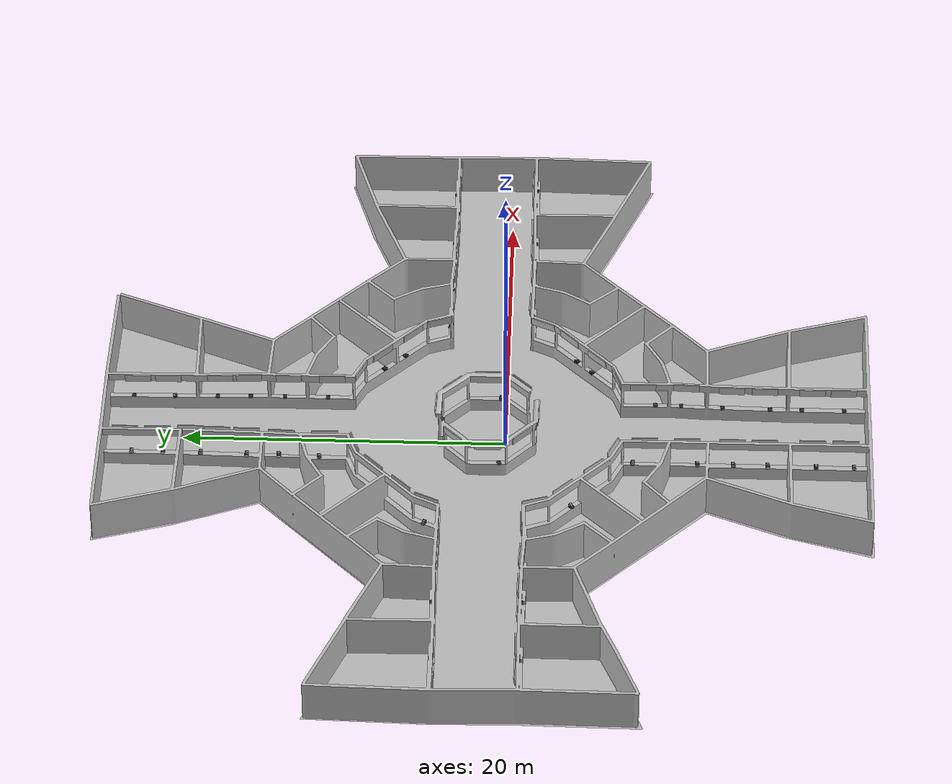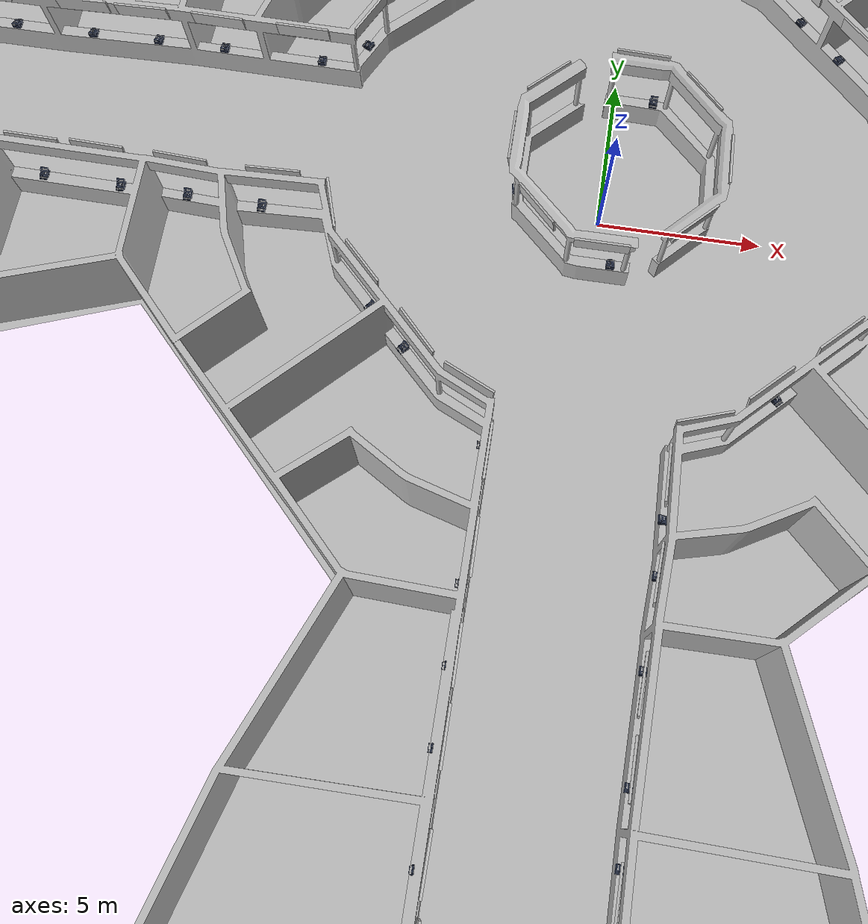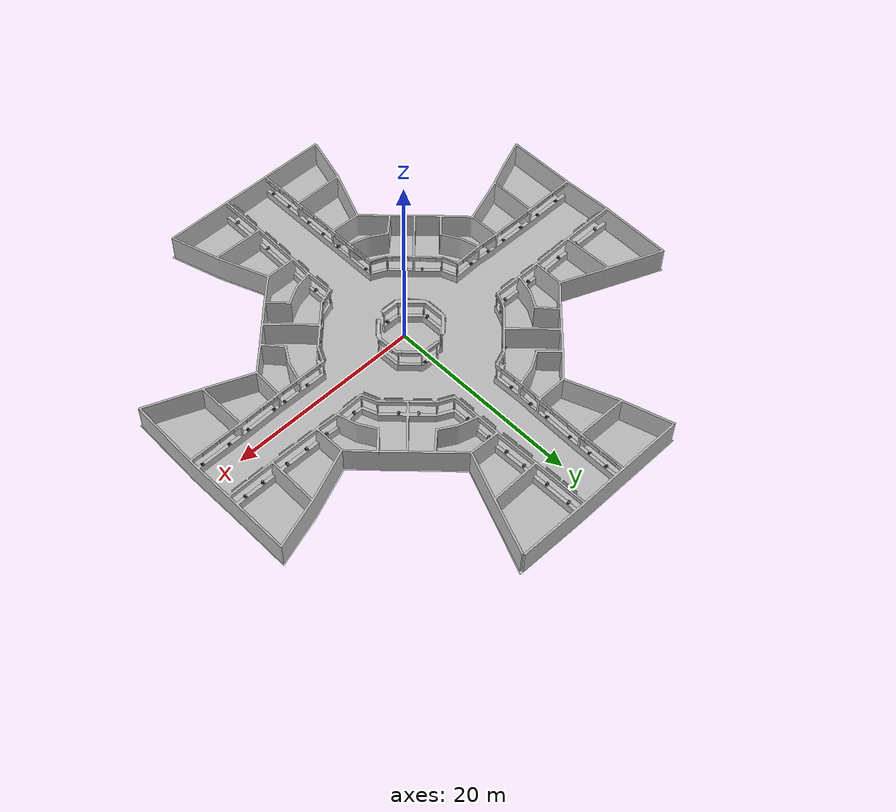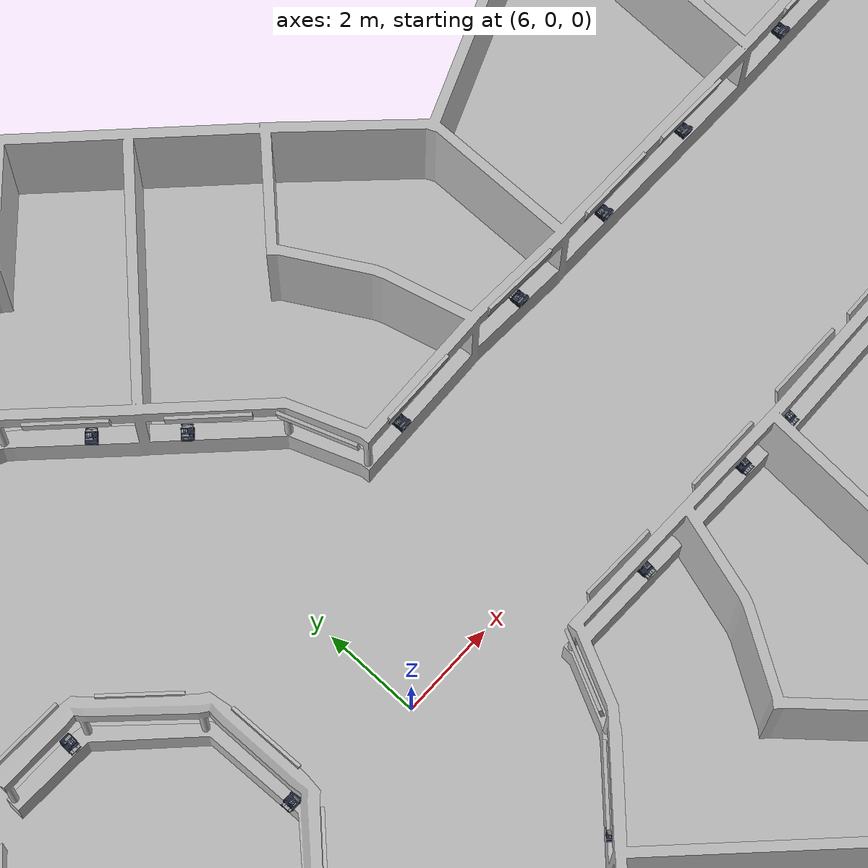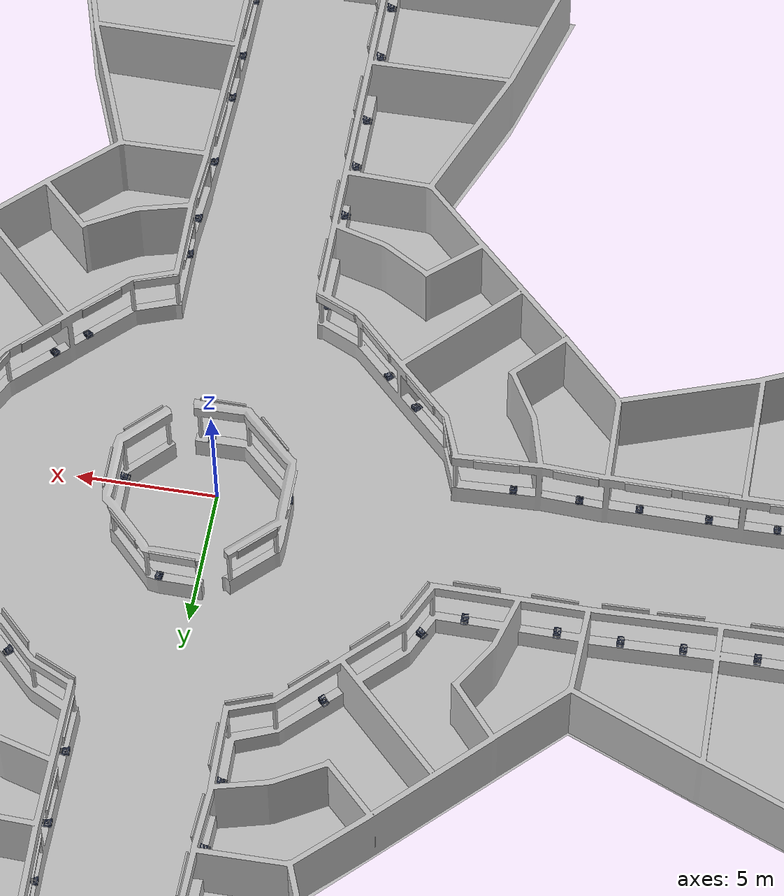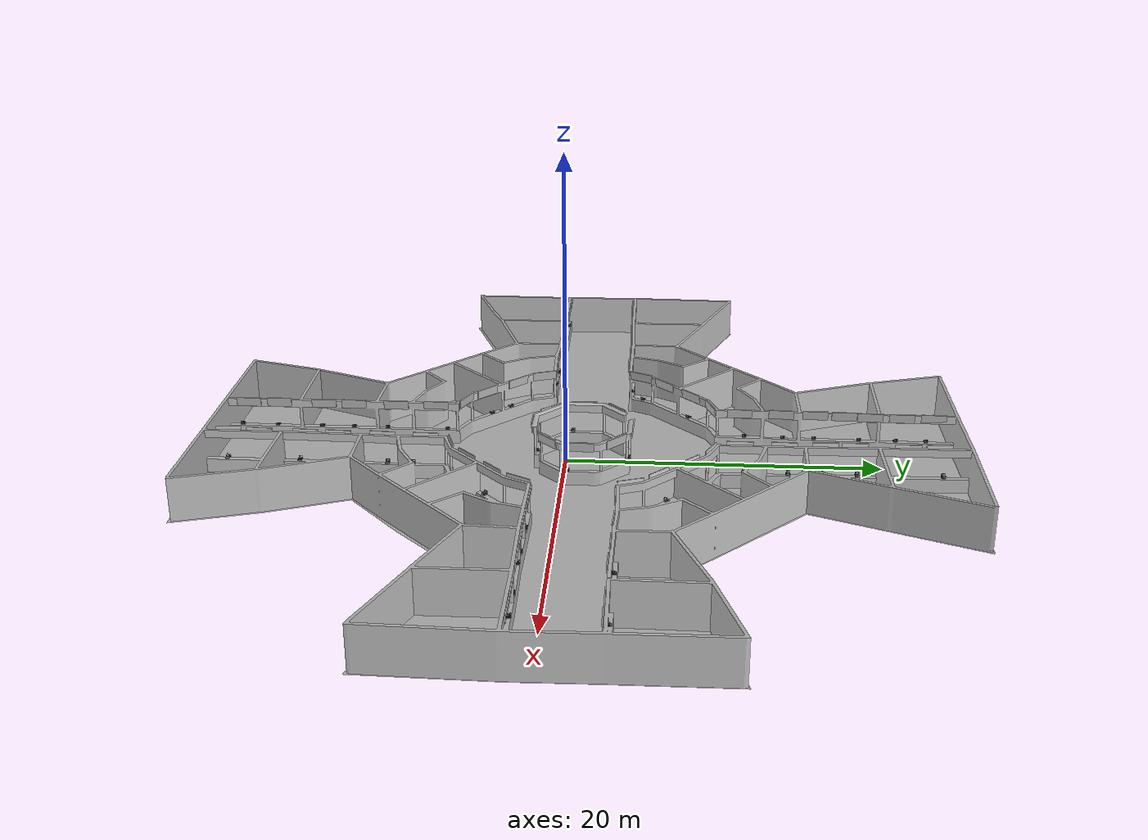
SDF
<sdf version="1.7">
 <world name="default">
  <light name="sun" type="directional">
   <pose>0 0 10 0 -0 0</pose>
   <diffuse>0.8 0.8 0.8 1</diffuse>
   <specular>0.2 0.2 0.2 1</specular>
   <attenuation>
    <range>1000</range>
    <constant>0.9</constant>
    <linear>0.01</linear>
    <quadratic>0.001</quadratic>
   </attenuation>
   <direction>-0.5 0.1 -0.9</direction>
   <spot><inner_angle>0</inner_angle><outer_angle>0</outer_angle><falloff>0</falloff></spot>
  </light>
  <model name="arena_hawker_centre_food_sign_1">
   <pose>-6.02755 10.6173 -1.87053 0.014789 0.032998 2.3489</pose>
   <static>1</static>
   <link name="body">
    <visual name="visual">
     <geometry>
      <mesh><uri>model://arena_hawker_centre_food_sign_1/media/arena_hawker_centre_food_sign_1.dae</uri></mesh>
     </geometry>
    </visual>
    <collision name="collision">
     <geometry>
      <mesh><uri>model://arena_hawker_centre_food_sign_1/media/arena_hawker_centre_food_sign_1.dae</uri></mesh>
     </geometry>
    </collision>
   </link>
  </model>
  <model name="arena_hawker_centre_food_sign_2">
   <pose>0.911927 0.209526 -1.76871 -0.004251 0.002016 0.779186</pose>
   <static>1</static>
   <link name="body">
    <visual name="visual">
     <geometry>
      <mesh><uri>model://arena_hawker_centre_food_sign_2/media/arena_hawker_centre_food_sign_2.dae</uri></mesh>
     </geometry>
    </visual>
    <collision name="collision">
     <geometry>
      <mesh><uri>model://arena_hawker_centre_food_sign_2/media/arena_hawker_centre_food_sign_2.dae</uri></mesh>
     </geometry>
    </collision>
   </link>
  </model>
  <model name="arena_hawker_centre_food_sign_2_clone">
   <pose>-5.04406 14.802 -1.80589 0.022985 0.004067 3.08736</pose>
   <static>1</static>
   <link name="body">
    <visual name="visual">
     <geometry>
      <mesh><uri>model://arena_hawker_centre_food_sign_2/media/arena_hawker_centre_food_sign_2.dae</uri></mesh>
     </geometry>
    </visual>
    <collision name="collision">
     <geometry>
      <mesh><uri>model://arena_hawker_centre_food_sign_2/media/arena_hawker_centre_food_sign_2.dae</uri></mesh>
     </geometry>
    </collision>
   </link>
  </model>
  <model name="arena_hawker_centre_food_sign_2_clone_0">
   <pose>-15.8076 6.67681 -1.81225 0.025401 0.003626 1.6036</pose>
   <static>1</static>
   <link name="body">
    <visual name="visual">
     <geometry>
      <mesh><uri>model://arena_hawker_centre_food_sign_2/media/arena_hawker_centre_food_sign_2.dae</uri></mesh>
     </geometry>
    </visual>
    <collision name="collision">
     <geometry>
      <mesh><uri>model://arena_hawker_centre_food_sign_2/media/arena_hawker_centre_food_sign_2.dae</uri></mesh>
     </geometry>
    </collision>
   </link>
  </model>
  <model name="arena_hawker_centre_food_sign_2_clone_1">
   <pose>-10.8907 -1.90369 -1.77323 0.004703 0.000119 -2.83057</pose>
   <static>1</static>
   <link name="body">
    <visual name="visual">
     <geometry>
      <mesh><uri>model://arena_hawker_centre_food_sign_2/media/arena_hawker_centre_food_sign_2.dae</uri></mesh>
     </geometry>
    </visual>
    <collision name="collision">
     <geometry>
      <mesh><uri>model://arena_hawker_centre_food_sign_2/media/arena_hawker_centre_food_sign_2.dae</uri></mesh>
     </geometry>
    </collision>
   </link>
  </model>
  <model name="arena_hawker_centre_food_sign_2_clone_2">
   <pose>-20.847 -4.08267 -1.74528 0.001484 -0.004465 -1.55531</pose>
   <static>1</static>
   <link name="body">
    <visual name="visual">
     <geometry>
      <mesh><uri>model://arena_hawker_centre_food_sign_2/media/arena_hawker_centre_food_sign_2.dae</uri></mesh>
     </geometry>
    </visual>
    <collision name="collision">
     <geometry>
      <mesh><uri>model://arena_hawker_centre_food_sign_2/media/arena_hawker_centre_food_sign_2.dae</uri></mesh>
     </geometry>
    </collision>
   </link>
  </model>
  <model name="arena_hawker_centre_food_sign_2_clone_3">
   <pose>5.30715 -20.1037 -1.76831 -0.004406 -0.001651 -0.022207</pose>
   <static>1</static>
   <link name="body">
    <visual name="visual">
     <geometry>
      <mesh><uri>model://arena_hawker_centre_food_sign_2/media/arena_hawker_centre_food_sign_2.dae</uri></mesh>
     </geometry>
    </visual>
    <collision name="collision">
     <geometry>
      <mesh><uri>model://arena_hawker_centre_food_sign_2/media/arena_hawker_centre_food_sign_2.dae</uri></mesh>
     </geometry>
    </collision>
   </link>
  </model>
  <model name="arena_hawker_centre_food_sign_2_clone_4">
   <pose>10.3568 -4.40728 -1.75301 -0.003314 -0.00334 -0.45298</pose>
   <static>1</static>
   <link name="body">
    <visual name="visual">
     <geometry>
      <mesh><uri>model://arena_hawker_centre_food_sign_2/media/arena_hawker_centre_food_sign_2.dae</uri></mesh>
     </geometry>
    </visual>
    <collision name="collision">
     <geometry>
      <mesh><uri>model://arena_hawker_centre_food_sign_2/media/arena_hawker_centre_food_sign_2.dae</uri></mesh>
     </geometry>
    </collision>
   </link>
  </model>
  <model name="arena_hawker_centre_food_sign_2_clone_5">
   <pose>21.7618 6.39417 -1.79854 0.015684 0.004659 1.58625</pose>
   <static>1</static>
   <link name="body">
    <visual name="visual">
     <geometry>
      <mesh><uri>model://arena_hawker_centre_food_sign_2/media/arena_hawker_centre_food_sign_2.dae</uri></mesh>
     </geometry>
    </visual>
    <collision name="collision">
     <geometry>
      <mesh><uri>model://arena_hawker_centre_food_sign_2/media/arena_hawker_centre_food_sign_2.dae</uri></mesh>
     </geometry>
    </collision>
   </link>
  </model>
  <model name="arena_hawker_centre_food_sign_2_clone_6">
   <pose>5.73289 11.3099 -1.77028 -0.003238 0.003414 1.14825</pose>
   <static>1</static>
   <link name="body">
    <visual name="visual">
     <geometry>
      <mesh><uri>model://arena_hawker_centre_food_sign_2/media/arena_hawker_centre_food_sign_2.dae</uri></mesh>
     </geometry>
    </visual>
    <collision name="collision">
     <geometry>
      <mesh><uri>model://arena_hawker_centre_food_sign_2/media/arena_hawker_centre_food_sign_2.dae</uri></mesh>
     </geometry>
    </collision>
   </link>
  </model>
  <model name="arena_hawker_centre_food_sign_3">
   <pose>-10.0416 6.68987 -1.74695 0.025512 0.000279 2.69859</pose>
   <static>1</static>
   <link name="body">
    <visual name="visual">
     <geometry>
      <mesh><uri>model://arena_hawker_centre_food_sign_3/media/arena_hawker_centre_food_sign_3.dae</uri></mesh>
     </geometry>
    </visual>
    <collision name="collision">
     <geometry>
      <mesh><uri>model://arena_hawker_centre_food_sign_3/media/arena_hawker_centre_food_sign_3.dae</uri></mesh>
     </geometry>
    </collision>
   </link>
  </model>
  <model name="arena_hawker_centre_food_sign_3_clone">
   <pose>-3.08768 12.2084 -1.85893 0.018122 0.01796 1.92871</pose>
   <static>1</static>
   <link name="body">
    <visual name="visual">
     <geometry>
      <mesh><uri>model://arena_hawker_centre_food_sign_3/media/arena_hawker_centre_food_sign_3.dae</uri></mesh>
     </geometry>
    </visual>
    <collision name="collision">
     <geometry>
      <mesh><uri>model://arena_hawker_centre_food_sign_3/media/arena_hawker_centre_food_sign_3.dae</uri></mesh>
     </geometry>
    </collision>
   </link>
  </model>
  <model name="arena_hawker_centre_food_sign_4">
   <pose>-0.280631 1.94164 -1.79429 0.014086 -0 -2.36084</pose>
   <static>1</static>
   <link name="body">
    <visual name="visual">
     <geometry>
      <mesh><uri>model://arena_hawker_centre_food_sign_4/media/arena_hawker_centre_food_sign_4.dae</uri></mesh>
     </geometry>
    </visual>
    <collision name="collision">
     <geometry>
      <mesh><uri>model://arena_hawker_centre_food_sign_4/media/arena_hawker_centre_food_sign_4.dae</uri></mesh>
     </geometry>
    </collision>
   </link>
  </model>
  <model name="arena_hawker_centre_food_sign_4_clone">
   <pose>5.54365 22.0322 -1.75761 0.021093 -0.010669 0.016324</pose>
   <static>1</static>
   <link name="body">
    <visual name="visual">
     <geometry>
      <mesh><uri>model://arena_hawker_centre_food_sign_4/media/arena_hawker_centre_food_sign_4.dae</uri></mesh>
     </geometry>
    </visual>
    <collision name="collision">
     <geometry>
      <mesh><uri>model://arena_hawker_centre_food_sign_4/media/arena_hawker_centre_food_sign_4.dae</uri></mesh>
     </geometry>
    </collision>
   </link>
  </model>
  <model name="arena_hawker_centre_food_sign_4_clone_0">
   <pose>-10.4498 -4.21475 -1.75784 0.022692 -0.010351 -1.53541</pose>
   <static>1</static>
   <link name="body">
    <visual name="visual">
     <geometry>
      <mesh><uri>model://arena_hawker_centre_food_sign_4/media/arena_hawker_centre_food_sign_4.dae</uri></mesh>
     </geometry>
    </visual>
    <collision name="collision">
     <geometry>
      <mesh><uri>model://arena_hawker_centre_food_sign_4/media/arena_hawker_centre_food_sign_4.dae</uri></mesh>
     </geometry>
    </collision>
   </link>
  </model>
  <model name="arena_hawker_centre_food_sign_4_clone_1">
   <pose>-5.13619 -14.9795 -1.80784 0.010009 0.009911 -3.14127</pose>
   <static>1</static>
   <link name="body">
    <visual name="visual">
     <geometry>
      <mesh><uri>model://arena_hawker_centre_food_sign_4/media/arena_hawker_centre_food_sign_4.dae</uri></mesh>
     </geometry>
    </visual>
    <collision name="collision">
     <geometry>
      <mesh><uri>model://arena_hawker_centre_food_sign_4/media/arena_hawker_centre_food_sign_4.dae</uri></mesh>
     </geometry>
    </collision>
   </link>
  </model>
  <model name="arena_hawker_centre_food_sign_4_clone_2">
   <pose>5.55772 -9.47702 -1.74272 0.007138 -0.009863 0.005118</pose>
   <static>1</static>
   <link name="body">
    <visual name="visual">
     <geometry>
      <mesh><uri>model://arena_hawker_centre_food_sign_4/media/arena_hawker_centre_food_sign_4.dae</uri></mesh>
     </geometry>
    </visual>
    <collision name="collision">
     <geometry>
      <mesh><uri>model://arena_hawker_centre_food_sign_4/media/arena_hawker_centre_food_sign_4.dae</uri></mesh>
     </geometry>
    </collision>
   </link>
  </model>
  <model name="arena_hawker_centre_food_sign_4_clone_3">
   <pose>16.1947 -4.32239 -1.74883 0.009653 -0.010258 -1.54508</pose>
   <static>1</static>
   <link name="body">
    <visual name="visual">
     <geometry>
      <mesh><uri>model://arena_hawker_centre_food_sign_4/media/arena_hawker_centre_food_sign_4.dae</uri></mesh>
     </geometry>
    </visual>
    <collision name="collision">
     <geometry>
      <mesh><uri>model://arena_hawker_centre_food_sign_4/media/arena_hawker_centre_food_sign_4.dae</uri></mesh>
     </geometry>
    </collision>
   </link>
  </model>
  <model name="arena_hawker_centre_food_sign_4_clone_4">
   <pose>10.9035 6.45495 -1.82681 0.022744 0.010185 1.58891</pose>
   <static>1</static>
   <link name="body">
    <visual name="visual">
     <geometry>
      <mesh><uri>model://arena_hawker_centre_food_sign_4/media/arena_hawker_centre_food_sign_4.dae</uri></mesh>
     </geometry>
    </visual>
    <collision name="collision">
     <geometry>
      <mesh><uri>model://arena_hawker_centre_food_sign_4/media/arena_hawker_centre_food_sign_4.dae</uri></mesh>
     </geometry>
    </collision>
   </link>
  </model>
  <model name="arena_hawker_centre_food_sign_4_clone_5">
   <pose>5.64203 16.9148 -1.71032 0.012676 -0.009646 0.026514</pose>
   <static>1</static>
   <link name="body">
    <visual name="visual">
     <geometry>
      <mesh><uri>model://arena_hawker_centre_food_sign_4/media/arena_hawker_centre_food_sign_4.dae</uri></mesh>
     </geometry>
    </visual>
    <collision name="collision">
     <geometry>
      <mesh><uri>model://arena_hawker_centre_food_sign_4/media/arena_hawker_centre_food_sign_4.dae</uri></mesh>
     </geometry>
    </collision>
   </link>
  </model>
  <model name="arena_hawker_centre_food_sign_5">
   <pose>0.483695 2.02864 -1.79638 0.0265 -0 -3.12356</pose>
   <static>1</static>
   <link name="body">
    <visual name="visual">
     <geometry>
      <mesh><uri>model://arena_hawker_centre_food_sign_5/media/arena_hawker_centre_food_sign_5.dae</uri></mesh>
     </geometry>
    </visual>
    <collision name="collision">
     <geometry>
      <mesh><uri>model://arena_hawker_centre_food_sign_5/media/arena_hawker_centre_food_sign_5.dae</uri></mesh>
     </geometry>
    </collision>
   </link>
  </model>
  <model name="arena_hawker_centre_food_sign_5_clone">
   <pose>-4.99484 24.2451 -1.81528 0.026499 0.000221 -3.1319</pose>
   <static>1</static>
   <link name="body">
    <visual name="visual">
     <geometry>
      <mesh><uri>model://arena_hawker_centre_food_sign_5/media/arena_hawker_centre_food_sign_5.dae</uri></mesh>
     </geometry>
    </visual>
    <collision name="collision">
     <geometry>
      <mesh><uri>model://arena_hawker_centre_food_sign_5/media/arena_hawker_centre_food_sign_5.dae</uri></mesh>
     </geometry>
    </collision>
   </link>
  </model>
  <model name="arena_hawker_centre_food_sign_5_clone_0">
   <pose>-5.2062 -7.68907 -1.7874 0.026495 0.000532 3.13956</pose>
   <static>1</static>
   <link name="body">
    <visual name="visual">
     <geometry>
      <mesh><uri>model://arena_hawker_centre_food_sign_5/media/arena_hawker_centre_food_sign_5.dae</uri></mesh>
     </geometry>
    </visual>
    <collision name="collision">
     <geometry>
      <mesh><uri>model://arena_hawker_centre_food_sign_5/media/arena_hawker_centre_food_sign_5.dae</uri></mesh>
     </geometry>
    </collision>
   </link>
  </model>
  <model name="arena_hawker_centre_food_sign_5_clone_1">
   <pose>-5.20647 -13.1061 -1.79638 0.026499 0.000226 -3.13208</pose>
   <static>1</static>
   <link name="body">
    <visual name="visual">
     <geometry>
      <mesh><uri>model://arena_hawker_centre_food_sign_5/media/arena_hawker_centre_food_sign_5.dae</uri></mesh>
     </geometry>
    </visual>
    <collision name="collision">
     <geometry>
      <mesh><uri>model://arena_hawker_centre_food_sign_5/media/arena_hawker_centre_food_sign_5.dae</uri></mesh>
     </geometry>
    </collision>
   </link>
  </model>
  <model name="arena_hawker_centre_food_sign_5_clone_2">
   <pose>5.4567 -12.2683 -1.75527 0.020298 0.000336 -0.050771</pose>
   <static>1</static>
   <link name="body">
    <visual name="visual">
     <geometry>
      <mesh><uri>model://arena_hawker_centre_food_sign_5/media/arena_hawker_centre_food_sign_5.dae</uri></mesh>
     </geometry>
    </visual>
    <collision name="collision">
     <geometry>
      <mesh><uri>model://arena_hawker_centre_food_sign_5/media/arena_hawker_centre_food_sign_5.dae</uri></mesh>
     </geometry>
    </collision>
   </link>
  </model>
  <model name="arena_hawker_centre_food_sign_5_clone_3">
   <pose>14.1418 -4.38549 -1.69789 0.011537 -0.026496 -1.56915</pose>
   <static>1</static>
   <link name="body">
    <visual name="visual">
     <geometry>
      <mesh><uri>model://arena_hawker_centre_food_sign_5/media/arena_hawker_centre_food_sign_5.dae</uri></mesh>
     </geometry>
    </visual>
    <collision name="collision">
     <geometry>
      <mesh><uri>model://arena_hawker_centre_food_sign_5/media/arena_hawker_centre_food_sign_5.dae</uri></mesh>
     </geometry>
    </collision>
   </link>
  </model>
  <model name="arena_hawker_centre_food_sign_5_clone_4">
   <pose>13.8705 6.3282 -1.86865 0.017765 0.026448 1.52621</pose>
   <static>1</static>
   <link name="body">
    <visual name="visual">
     <geometry>
      <mesh><uri>model://arena_hawker_centre_food_sign_5/media/arena_hawker_centre_food_sign_5.dae</uri></mesh>
     </geometry>
    </visual>
    <collision name="collision">
     <geometry>
      <mesh><uri>model://arena_hawker_centre_food_sign_5/media/arena_hawker_centre_food_sign_5.dae</uri></mesh>
     </geometry>
    </collision>
   </link>
  </model>
  <model name="arena_hawker_centre_food_sign_5_clone_5">
   <pose>5.65989 15.2112 -1.73341 0.022626 0.00063 0.041796</pose>
   <static>1</static>
   <link name="body">
    <visual name="visual">
     <geometry>
      <mesh><uri>model://arena_hawker_centre_food_sign_5/media/arena_hawker_centre_food_sign_5.dae</uri></mesh>
     </geometry>
    </visual>
    <collision name="collision">
     <geometry>
      <mesh><uri>model://arena_hawker_centre_food_sign_5/media/arena_hawker_centre_food_sign_5.dae</uri></mesh>
     </geometry>
    </collision>
   </link>
  </model>
  <model name="arena_hawker_centre_food_sign_6">
   <pose>0.02993 0.092063 -1.83428 0.023472 -0 0</pose>
   <static>1</static>
   <link name="body">
    <visual name="visual">
     <geometry>
      <mesh><uri>model://arena_hawker_centre_food_sign_6/media/arena_hawker_centre_food_sign_6.dae</uri></mesh>
     </geometry>
    </visual>
    <collision name="collision">
     <geometry>
      <mesh><uri>model://arena_hawker_centre_food_sign_6/media/arena_hawker_centre_food_sign_6.dae</uri></mesh>
     </geometry>
    </collision>
   </link>
  </model>
  <model name="arena_hawker_centre_food_sign_6_clone">
   <pose>-5.13236 11.9711 -1.79234 0.018006 -0.000219 -3.12976</pose>
   <static>1</static>
   <link name="body">
    <visual name="visual">
     <geometry>
      <mesh><uri>model://arena_hawker_centre_food_sign_6/media/arena_hawker_centre_food_sign_6.dae</uri></mesh>
     </geometry>
    </visual>
    <collision name="collision">
     <geometry>
      <mesh><uri>model://arena_hawker_centre_food_sign_6/media/arena_hawker_centre_food_sign_6.dae</uri></mesh>
     </geometry>
    </collision>
   </link>
  </model>
  <model name="arena_hawker_centre_food_sign_6_clone_0">
   <pose>-13.8593 6.80778 -1.70274 0.015163 -0.023466 1.59264</pose>
   <static>1</static>
   <link name="body">
    <visual name="visual">
     <geometry>
      <mesh><uri>model://arena_hawker_centre_food_sign_6/media/arena_hawker_centre_food_sign_6.dae</uri></mesh>
     </geometry>
    </visual>
    <collision name="collision">
     <geometry>
      <mesh><uri>model://arena_hawker_centre_food_sign_6/media/arena_hawker_centre_food_sign_6.dae</uri></mesh>
     </geometry>
    </collision>
   </link>
  </model>
  <model name="arena_hawker_centre_food_sign_6_clone_1">
   <pose>-9.25321 -5.01915 -1.8325 0.025187 0.015767 -2.36144</pose>
   <static>1</static>
   <link name="body">
    <visual name="visual">
     <geometry>
      <mesh><uri>model://arena_hawker_centre_food_sign_6/media/arena_hawker_centre_food_sign_6.dae</uri></mesh>
     </geometry>
    </visual>
    <collision name="collision">
     <geometry>
      <mesh><uri>model://arena_hawker_centre_food_sign_6/media/arena_hawker_centre_food_sign_6.dae</uri></mesh>
     </geometry>
    </collision>
   </link>
  </model>
  <model name="arena_hawker_centre_food_sign_6_clone_2">
   <pose>-17.8621 -3.98273 -1.85386 0.009701 0.023471 -1.57897</pose>
   <static>1</static>
   <link name="body">
    <visual name="visual">
     <geometry>
      <mesh><uri>model://arena_hawker_centre_food_sign_6/media/arena_hawker_centre_food_sign_6.dae</uri></mesh>
     </geometry>
    </visual>
    <collision name="collision">
     <geometry>
      <mesh><uri>model://arena_hawker_centre_food_sign_6/media/arena_hawker_centre_food_sign_6.dae</uri></mesh>
     </geometry>
    </collision>
   </link>
  </model>
  <model name="arena_hawker_centre_food_sign_6_clone_3">
   <pose>5.31505 -21.8164 -1.76763 0.023468 -0.000428 0.01825</pose>
   <static>1</static>
   <link name="body">
    <visual name="visual">
     <geometry>
      <mesh><uri>model://arena_hawker_centre_food_sign_6/media/arena_hawker_centre_food_sign_6.dae</uri></mesh>
     </geometry>
    </visual>
    <collision name="collision">
     <geometry>
      <mesh><uri>model://arena_hawker_centre_food_sign_6/media/arena_hawker_centre_food_sign_6.dae</uri></mesh>
     </geometry>
    </collision>
   </link>
  </model>
  <model name="arena_hawker_centre_food_sign_6_clone_4">
   <pose>8.20841 -6.56149 -1.83238 0.016386 0.016807 -0.797999</pose>
   <static>1</static>
   <link name="body">
    <visual name="visual">
     <geometry>
      <mesh><uri>model://arena_hawker_centre_food_sign_6/media/arena_hawker_centre_food_sign_6.dae</uri></mesh>
     </geometry>
    </visual>
    <collision name="collision">
     <geometry>
      <mesh><uri>model://arena_hawker_centre_food_sign_6/media/arena_hawker_centre_food_sign_6.dae</uri></mesh>
     </geometry>
    </collision>
   </link>
  </model>
  <model name="arena_hawker_centre_food_sign_6_clone_5">
   <pose>23.6105 6.49971 -1.70901 0.016751 -0.023543 1.57723</pose>
   <static>1</static>
   <link name="body">
    <visual name="visual">
     <geometry>
      <mesh><uri>model://arena_hawker_centre_food_sign_6/media/arena_hawker_centre_food_sign_6.dae</uri></mesh>
     </geometry>
    </visual>
    <collision name="collision">
     <geometry>
      <mesh><uri>model://arena_hawker_centre_food_sign_6/media/arena_hawker_centre_food_sign_6.dae</uri></mesh>
     </geometry>
    </collision>
   </link>
  </model>
  <model name="arena_hawker_centre_food_sign_6_clone_6">
   <pose>8.03737 9.24896 -1.73557 0.016542 -0.016653 0.788664</pose>
   <static>1</static>
   <link name="body">
    <visual name="visual">
     <geometry>
      <mesh><uri>model://arena_hawker_centre_food_sign_6/media/arena_hawker_centre_food_sign_6.dae</uri></mesh>
     </geometry>
    </visual>
    <collision name="collision">
     <geometry>
      <mesh><uri>model://arena_hawker_centre_food_sign_6/media/arena_hawker_centre_food_sign_6.dae</uri></mesh>
     </geometry>
    </collision>
   </link>
  </model>
  <model name="arena_hawker_centre_food_sign_7">
   <pose>-7.96268 8.91472 -1.77143 0.02281 0 2.36863</pose>
   <static>1</static>
   <link name="body">
    <visual name="visual">
     <geometry>
      <mesh><uri>model://arena_hawker_centre_food_sign_7/media/arena_hawker_centre_food_sign_7.dae</uri></mesh>
     </geometry>
    </visual>
    <collision name="collision">
     <geometry>
      <mesh><uri>model://arena_hawker_centre_food_sign_7/media/arena_hawker_centre_food_sign_7.dae</uri></mesh>
     </geometry>
    </collision>
   </link>
  </model>
  <model name="arena_hawker_centre_food_sign_8">
   <pose>-0.448368 1.3756 -1.733 0.019862 -0 -1.60044</pose>
   <static>1</static>
   <link name="body">
    <visual name="visual">
     <geometry>
      <mesh><uri>model://arena_hawker_centre_food_sign_8/media/arena_hawker_centre_food_sign_8.dae</uri></mesh>
     </geometry>
    </visual>
    <collision name="collision">
     <geometry>
      <mesh><uri>model://arena_hawker_centre_food_sign_8/media/arena_hawker_centre_food_sign_8.dae</uri></mesh>
     </geometry>
    </collision>
   </link>
  </model>
  <model name="arena_hawker_centre_food_sign_8_clone">
   <pose>-8.75875 6.67026 -1.7578 0.021511 0.00043 1.56282</pose>
   <static>1</static>
   <link name="body">
    <visual name="visual">
     <geometry>
      <mesh><uri>model://arena_hawker_centre_food_sign_8/media/arena_hawker_centre_food_sign_8.dae</uri></mesh>
     </geometry>
    </visual>
    <collision name="collision">
     <geometry>
      <mesh><uri>model://arena_hawker_centre_food_sign_8/media/arena_hawker_centre_food_sign_8.dae</uri></mesh>
     </geometry>
    </collision>
   </link>
  </model>
  <model name="arena_hawker_centre_food_sign_8_clone_0">
   <pose>-13.4683 -4.07029 -1.78455 0.019858 0.000417 -1.62143</pose>
   <static>1</static>
   <link name="body">
    <visual name="visual">
     <geometry>
      <mesh><uri>model://arena_hawker_centre_food_sign_8/media/arena_hawker_centre_food_sign_8.dae</uri></mesh>
     </geometry>
    </visual>
    <collision name="collision">
     <geometry>
      <mesh><uri>model://arena_hawker_centre_food_sign_8/media/arena_hawker_centre_food_sign_8.dae</uri></mesh>
     </geometry>
    </collision>
   </link>
  </model>
  <model name="arena_hawker_centre_food_sign_8_clone_1">
   <pose>-5.07355 -17.9378 -1.82853 0.018928 0.019858 3.13089</pose>
   <static>1</static>
   <link name="body">
    <visual name="visual">
     <geometry>
      <mesh><uri>model://arena_hawker_centre_food_sign_8/media/arena_hawker_centre_food_sign_8.dae</uri></mesh>
     </geometry>
    </visual>
    <collision name="collision">
     <geometry>
      <mesh><uri>model://arena_hawker_centre_food_sign_8/media/arena_hawker_centre_food_sign_8.dae</uri></mesh>
     </geometry>
    </collision>
   </link>
  </model>
  <model name="arena_hawker_centre_food_sign_8_clone_2">
   <pose>3.44313 -9.93766 -1.79386 0.018615 -0.006928 -1.24421</pose>
   <static>1</static>
   <link name="body">
    <visual name="visual">
     <geometry>
      <mesh><uri>model://arena_hawker_centre_food_sign_8/media/arena_hawker_centre_food_sign_8.dae</uri></mesh>
     </geometry>
    </visual>
    <collision name="collision">
     <geometry>
      <mesh><uri>model://arena_hawker_centre_food_sign_8/media/arena_hawker_centre_food_sign_8.dae</uri></mesh>
     </geometry>
    </collision>
   </link>
  </model>
  <model name="arena_hawker_centre_food_sign_8_clone_3">
   <pose>19.2209 -4.24369 -1.78238 0.019844 -0.000854 -1.55744</pose>
   <static>1</static>
   <link name="body">
    <visual name="visual">
     <geometry>
      <mesh><uri>model://arena_hawker_centre_food_sign_8/media/arena_hawker_centre_food_sign_8.dae</uri></mesh>
     </geometry>
    </visual>
    <collision name="collision">
     <geometry>
      <mesh><uri>model://arena_hawker_centre_food_sign_8/media/arena_hawker_centre_food_sign_8.dae</uri></mesh>
     </geometry>
    </collision>
   </link>
  </model>
  <model name="arena_hawker_centre_food_sign_8_clone_4">
   <pose>11.3942 4.50456 -1.72443 0.023659 -0.020527 0.345661</pose>
   <static>1</static>
   <link name="body">
    <visual name="visual">
     <geometry>
      <mesh><uri>model://arena_hawker_centre_food_sign_8/media/arena_hawker_centre_food_sign_8.dae</uri></mesh>
     </geometry>
    </visual>
    <collision name="collision">
     <geometry>
      <mesh><uri>model://arena_hawker_centre_food_sign_8/media/arena_hawker_centre_food_sign_8.dae</uri></mesh>
     </geometry>
    </collision>
   </link>
  </model>
  <model name="arena_hawker_centre_food_sign_8_clone_5">
   <pose>5.61372 20.1638 -1.74057 0.025403 -0.019842 0.015695</pose>
   <static>1</static>
   <link name="body">
    <visual name="visual">
     <geometry>
      <mesh><uri>model://arena_hawker_centre_food_sign_8/media/arena_hawker_centre_food_sign_8.dae</uri></mesh>
     </geometry>
    </visual>
    <collision name="collision">
     <geometry>
      <mesh><uri>model://arena_hawker_centre_food_sign_8/media/arena_hawker_centre_food_sign_8.dae</uri></mesh>
     </geometry>
    </collision>
   </link>
  </model>
  <model name="arena_hawker_centre_food_sign_9">
   <pose>1.19233 1.74773 -1.78132 0.027272 -0 2.36224</pose>
   <static>1</static>
   <link name="body">
    <visual name="visual">
     <geometry>
      <mesh><uri>model://arena_hawker_centre_food_sign_9/media/arena_hawker_centre_food_sign_9.dae</uri></mesh>
     </geometry>
    </visual>
    <collision name="collision">
     <geometry>
      <mesh><uri>model://arena_hawker_centre_food_sign_9/media/arena_hawker_centre_food_sign_9.dae</uri></mesh>
     </geometry>
    </collision>
   </link>
  </model>
  <model name="arena_hawker_centre_food_sign_9_clone">
   <pose>-5.11528 16.849 -1.70444 0.019631 -0.018932 3.12941</pose>
   <static>1</static>
   <link name="body">
    <visual name="visual">
     <geometry>
      <mesh><uri>model://arena_hawker_centre_food_sign_9/media/arena_hawker_centre_food_sign_9.dae</uri></mesh>
     </geometry>
    </visual>
    <collision name="collision">
     <geometry>
      <mesh><uri>model://arena_hawker_centre_food_sign_9/media/arena_hawker_centre_food_sign_9.dae</uri></mesh>
     </geometry>
    </collision>
   </link>
  </model>
  <model name="arena_hawker_centre_food_sign_9_clone_clone">
   <pose>-5.0561 18.6897 -1.70841 0.019631 -0.018932 3.12941</pose>
   <static>1</static>
   <link name="body">
    <visual name="visual">
     <geometry>
      <mesh><uri>model://arena_hawker_centre_food_sign_9/media/arena_hawker_centre_food_sign_9.dae</uri></mesh>
     </geometry>
    </visual>
    <collision name="collision">
     <geometry>
      <mesh><uri>model://arena_hawker_centre_food_sign_9/media/arena_hawker_centre_food_sign_9.dae</uri></mesh>
     </geometry>
    </collision>
   </link>
  </model>
  <model name="arena_hawker_centre_food_sign_9_clone_clone_clone">
   <pose>-4.98218 20.325 -1.70841 0.019631 -0.018932 3.12941</pose>
   <static>1</static>
   <link name="body">
    <visual name="visual">
     <geometry>
      <mesh><uri>model://arena_hawker_centre_food_sign_9/media/arena_hawker_centre_food_sign_9.dae</uri></mesh>
     </geometry>
    </visual>
    <collision name="collision">
     <geometry>
      <mesh><uri>model://arena_hawker_centre_food_sign_9/media/arena_hawker_centre_food_sign_9.dae</uri></mesh>
     </geometry>
    </collision>
   </link>
  </model>
  <model name="arena_hawker_centre_food_sign_9_clone_0">
   <pose>-20.7781 6.48283 -1.83199 0.018582 0.019963 1.5411</pose>
   <static>1</static>
   <link name="body">
    <visual name="visual">
     <geometry>
      <mesh><uri>model://arena_hawker_centre_food_sign_9/media/arena_hawker_centre_food_sign_9.dae</uri></mesh>
     </geometry>
    </visual>
    <collision name="collision">
     <geometry>
      <mesh><uri>model://arena_hawker_centre_food_sign_9/media/arena_hawker_centre_food_sign_9.dae</uri></mesh>
     </geometry>
    </collision>
   </link>
  </model>
  <model name="arena_hawker_centre_food_sign_9_clone_1">
   <pose>-5.20061 -9.07448 -1.62199 0.01402 -0.02575 -1.99707</pose>
   <static>1</static>
   <link name="body">
    <visual name="visual">
     <geometry>
      <mesh><uri>model://arena_hawker_centre_food_sign_9/media/arena_hawker_centre_food_sign_9.dae</uri></mesh>
     </geometry>
    </visual>
    <collision name="collision">
     <geometry>
      <mesh><uri>model://arena_hawker_centre_food_sign_9/media/arena_hawker_centre_food_sign_9.dae</uri></mesh>
     </geometry>
    </collision>
   </link>
  </model>
  <model name="arena_hawker_centre_food_sign_9_clone_2">
   <pose>-5.28206 -10.3862 -1.74093 0.035348 -0.019458 -3.12662</pose>
   <static>1</static>
   <link name="body">
    <visual name="visual">
     <geometry>
      <mesh><uri>model://arena_hawker_centre_food_sign_9/media/arena_hawker_centre_food_sign_9.dae</uri></mesh>
     </geometry>
    </visual>
    <collision name="collision">
     <geometry>
      <mesh><uri>model://arena_hawker_centre_food_sign_9/media/arena_hawker_centre_food_sign_9.dae</uri></mesh>
     </geometry>
    </collision>
   </link>
  </model>
  <model name="arena_hawker_centre_food_sign_9_clone_3">
   <pose>5.26905 -15.0862 -1.85308 0.014069 0.018361 -0.040896</pose>
   <static>1</static>
   <link name="body">
    <visual name="visual">
     <geometry>
      <mesh><uri>model://arena_hawker_centre_food_sign_9/media/arena_hawker_centre_food_sign_9.dae</uri></mesh>
     </geometry>
    </visual>
    <collision name="collision">
     <geometry>
      <mesh><uri>model://arena_hawker_centre_food_sign_9/media/arena_hawker_centre_food_sign_9.dae</uri></mesh>
     </geometry>
    </collision>
   </link>
  </model>
  <model name="arena_hawker_centre_food_sign_9_clone_4">
   <pose>11.7524 -4.39557 -1.72976 0.003926 -0.019613 -1.58184</pose>
   <static>1</static>
   <link name="body">
    <visual name="visual">
     <geometry>
      <mesh><uri>model://arena_hawker_centre_food_sign_9/media/arena_hawker_centre_food_sign_9.dae</uri></mesh>
     </geometry>
    </visual>
    <collision name="collision">
     <geometry>
      <mesh><uri>model://arena_hawker_centre_food_sign_9/media/arena_hawker_centre_food_sign_9.dae</uri></mesh>
     </geometry>
    </collision>
   </link>
  </model>
  <model name="arena_hawker_centre_food_sign_9_clone_5">
   <pose>16.2586 6.34384 -1.84249 0.029815 0.020203 1.5673</pose>
   <static>1</static>
   <link name="body">
    <visual name="visual">
     <geometry>
      <mesh><uri>model://arena_hawker_centre_food_sign_9/media/arena_hawker_centre_food_sign_9.dae</uri></mesh>
     </geometry>
    </visual>
    <collision name="collision">
     <geometry>
      <mesh><uri>model://arena_hawker_centre_food_sign_9/media/arena_hawker_centre_food_sign_9.dae</uri></mesh>
     </geometry>
    </collision>
   </link>
  </model>
  <model name="arena_hawker_centre_food_sign_9_clone_6">
   <pose>5.56532 12.5264 -1.79934 0.004693 0.018724 -0.003191</pose>
   <static>1</static>
   <link name="body">
    <visual name="visual">
     <geometry>
      <mesh><uri>model://arena_hawker_centre_food_sign_9/media/arena_hawker_centre_food_sign_9.dae</uri></mesh>
     </geometry>
    </visual>
    <collision name="collision">
     <geometry>
      <mesh><uri>model://arena_hawker_centre_food_sign_9/media/arena_hawker_centre_food_sign_9.dae</uri></mesh>
     </geometry>
    </collision>
   </link>
  </model>
  <model name="arena_hawker_centre_food_sign_10">
   <pose>-0.759998 0.399154 -1.78433 0.019601 0.002991 -0.801539</pose>
   <static>1</static>
   <link name="body">
    <visual name="visual">
     <geometry>
      <mesh><uri>model://arena_hawker_centre_food_sign_10/media/arena_hawker_centre_food_sign_10.dae</uri></mesh>
     </geometry>
    </visual>
    <collision name="collision">
     <geometry>
      <mesh><uri>model://arena_hawker_centre_food_sign_10/media/arena_hawker_centre_food_sign_10.dae</uri></mesh>
     </geometry>
    </collision>
   </link>
  </model>
  <model name="arena_hawker_centre_food_sign_10_clone">
   <pose>-11.3316 6.77249 -1.7527 0.012626 -0.016273 1.54805</pose>
   <static>1</static>
   <link name="body">
    <visual name="visual">
     <geometry>
      <mesh><uri>model://arena_hawker_centre_food_sign_10/media/arena_hawker_centre_food_sign_10.dae</uri></mesh>
     </geometry>
    </visual>
    <collision name="collision">
     <geometry>
      <mesh><uri>model://arena_hawker_centre_food_sign_10/media/arena_hawker_centre_food_sign_10.dae</uri></mesh>
     </geometry>
    </collision>
   </link>
  </model>
  <model name="arena_hawker_centre_food_sign_10_clone_0">
   <pose>-15.9183 -3.98659 -1.82387 0.011697 0.01601 -1.58992</pose>
   <static>1</static>
   <link name="body">
    <visual name="visual">
     <geometry>
      <mesh><uri>model://arena_hawker_centre_food_sign_10/media/arena_hawker_centre_food_sign_10.dae</uri></mesh>
     </geometry>
    </visual>
    <collision name="collision">
     <geometry>
      <mesh><uri>model://arena_hawker_centre_food_sign_10/media/arena_hawker_centre_food_sign_10.dae</uri></mesh>
     </geometry>
    </collision>
   </link>
  </model>
  <model name="arena_hawker_centre_food_sign_10_clone_1">
   <pose>-5.06524 -19.8767 -1.80664 0.0116 0.011002 3.11367</pose>
   <static>1</static>
   <link name="body">
    <visual name="visual">
     <geometry>
      <mesh><uri>model://arena_hawker_centre_food_sign_10/media/arena_hawker_centre_food_sign_10.dae</uri></mesh>
     </geometry>
    </visual>
    <collision name="collision">
     <geometry>
      <mesh><uri>model://arena_hawker_centre_food_sign_10/media/arena_hawker_centre_food_sign_10.dae</uri></mesh>
     </geometry>
    </collision>
   </link>
  </model>
  <model name="arena_hawker_centre_food_sign_10_clone_2">
   <pose>6.45206 -8.35475 -1.8 0.019601 0.002991 -0.801539</pose>
   <static>1</static>
   <link name="body">
    <visual name="visual">
     <geometry>
      <mesh><uri>model://arena_hawker_centre_food_sign_10/media/arena_hawker_centre_food_sign_10.dae</uri></mesh>
     </geometry>
    </visual>
    <collision name="collision">
     <geometry>
      <mesh><uri>model://arena_hawker_centre_food_sign_10/media/arena_hawker_centre_food_sign_10.dae</uri></mesh>
     </geometry>
    </collision>
   </link>
  </model>
  <model name="arena_hawker_centre_food_sign_10_clone_3">
   <pose>21.0701 -4.12748 -1.82235 0.011848 0.015899 -1.58043</pose>
   <static>1</static>
   <link name="body">
    <visual name="visual">
     <geometry>
      <mesh><uri>model://arena_hawker_centre_food_sign_10/media/arena_hawker_centre_food_sign_10.dae</uri></mesh>
     </geometry>
    </visual>
    <collision name="collision">
     <geometry>
      <mesh><uri>model://arena_hawker_centre_food_sign_10/media/arena_hawker_centre_food_sign_10.dae</uri></mesh>
     </geometry>
    </collision>
   </link>
  </model>
  <model name="arena_hawker_centre_food_sign_10_clone_4">
   <pose>9.87091 7.44162 -1.69403 0.017833 -0.019662 0.791021</pose>
   <static>1</static>
   <link name="body">
    <visual name="visual">
     <geometry>
      <mesh><uri>model://arena_hawker_centre_food_sign_10/media/arena_hawker_centre_food_sign_10.dae</uri></mesh>
     </geometry>
    </visual>
    <collision name="collision">
     <geometry>
      <mesh><uri>model://arena_hawker_centre_food_sign_10/media/arena_hawker_centre_food_sign_10.dae</uri></mesh>
     </geometry>
    </collision>
   </link>
  </model>
  <model name="arena_hawker_centre_food_sign_11">
   <pose>1.08755 0.870969 -1.7697 0.008593 -0 1.56384</pose>
   <static>1</static>
   <link name="body">
    <visual name="visual">
     <geometry>
      <mesh><uri>model://arena_hawker_centre_food_sign_11/media/arena_hawker_centre_food_sign_11.dae</uri></mesh>
     </geometry>
    </visual>
    <collision name="collision">
     <geometry>
      <mesh><uri>model://arena_hawker_centre_food_sign_11/media/arena_hawker_centre_food_sign_11.dae</uri></mesh>
     </geometry>
    </collision>
   </link>
  </model>
  <model name="arena_hawker_centre_food_sign_11_clone">
   <pose>-5.00603 22.2076 -1.78746 0.031621 -0.008591 -3.12847</pose>
   <static>1</static>
   <link name="body">
    <visual name="visual">
     <geometry>
      <mesh><uri>model://arena_hawker_centre_food_sign_11/media/arena_hawker_centre_food_sign_11.dae</uri></mesh>
     </geometry>
    </visual>
    <collision name="collision">
     <geometry>
      <mesh><uri>model://arena_hawker_centre_food_sign_11/media/arena_hawker_centre_food_sign_11.dae</uri></mesh>
     </geometry>
    </collision>
   </link>
  </model>
  <model name="arena_hawker_centre_food_sign_11_clone_0">
   <pose>-18.8612 6.62019 -1.78002 0.022248 -0.000132 1.57923</pose>
   <static>1</static>
   <link name="body">
    <visual name="visual">
     <geometry>
      <mesh><uri>model://arena_hawker_centre_food_sign_11/media/arena_hawker_centre_food_sign_11.dae</uri></mesh>
     </geometry>
    </visual>
    <collision name="collision">
     <geometry>
      <mesh><uri>model://arena_hawker_centre_food_sign_11/media/arena_hawker_centre_food_sign_11.dae</uri></mesh>
     </geometry>
    </collision>
   </link>
  </model>
  <model name="arena_hawker_centre_food_sign_11_clone_1">
   <pose>-7.52891 -6.85337 -1.73962 0.00812 -0.006157 -2.37659</pose>
   <static>1</static>
   <link name="body">
    <visual name="visual">
     <geometry>
      <mesh><uri>model://arena_hawker_centre_food_sign_11/media/arena_hawker_centre_food_sign_11.dae</uri></mesh>
     </geometry>
    </visual>
    <collision name="collision">
     <geometry>
      <mesh><uri>model://arena_hawker_centre_food_sign_11/media/arena_hawker_centre_food_sign_11.dae</uri></mesh>
     </geometry>
    </collision>
   </link>
  </model>
  <model name="arena_hawker_centre_food_sign_11_clone_2">
   <pose>-22.9691 -4.05824 -1.74633 0.014939 -0.00018 -1.57551</pose>
   <static>1</static>
   <link name="body">
    <visual name="visual">
     <geometry>
      <mesh><uri>model://arena_hawker_centre_food_sign_11/media/arena_hawker_centre_food_sign_11.dae</uri></mesh>
     </geometry>
    </visual>
    <collision name="collision">
     <geometry>
      <mesh><uri>model://arena_hawker_centre_food_sign_11/media/arena_hawker_centre_food_sign_11.dae</uri></mesh>
     </geometry>
    </collision>
   </link>
  </model>
  <model name="arena_hawker_centre_food_sign_11_clone_3">
   <pose>5.30881 -17.1373 -1.80749 -0.000103 0.008592 -0.018907</pose>
   <static>1</static>
   <link name="body">
    <visual name="visual">
     <geometry>
      <mesh><uri>model://arena_hawker_centre_food_sign_11/media/arena_hawker_centre_food_sign_11.dae</uri></mesh>
     </geometry>
    </visual>
    <collision name="collision">
     <geometry>
      <mesh><uri>model://arena_hawker_centre_food_sign_11/media/arena_hawker_centre_food_sign_11.dae</uri></mesh>
     </geometry>
    </collision>
   </link>
  </model>
  <model name="arena_hawker_centre_food_sign_11_clone_4">
   <pose>8.94347 -4.24368 -1.75855 0.004647 -0.000131 -1.59294</pose>
   <static>1</static>
   <link name="body">
    <visual name="visual">
     <geometry>
      <mesh><uri>model://arena_hawker_centre_food_sign_11/media/arena_hawker_centre_food_sign_11.dae</uri></mesh>
     </geometry>
    </visual>
    <collision name="collision">
     <geometry>
      <mesh><uri>model://arena_hawker_centre_food_sign_11/media/arena_hawker_centre_food_sign_11.dae</uri></mesh>
     </geometry>
    </collision>
   </link>
  </model>
  <model name="arena_hawker_centre_food_sign_11_clone_5">
   <pose>18.3766 6.35918 -1.78909 0.024598 0.000146 1.54685</pose>
   <static>1</static>
   <link name="body">
    <visual name="visual">
     <geometry>
      <mesh><uri>model://arena_hawker_centre_food_sign_11/media/arena_hawker_centre_food_sign_11.dae</uri></mesh>
     </geometry>
    </visual>
    <collision name="collision">
     <geometry>
      <mesh><uri>model://arena_hawker_centre_food_sign_11/media/arena_hawker_centre_food_sign_11.dae</uri></mesh>
     </geometry>
    </collision>
   </link>
  </model>
  <model name="arena_hawker_centre_food_sign_11_clone_6">
   <pose>5.66056 9.91152 -1.78378 0.01757 0.008592 0.007021</pose>
   <static>1</static>
   <link name="body">
    <visual name="visual">
     <geometry>
      <mesh><uri>model://arena_hawker_centre_food_sign_11/media/arena_hawker_centre_food_sign_11.dae</uri></mesh>
     </geometry>
    </visual>
    <collision name="collision">
     <geometry>
      <mesh><uri>model://arena_hawker_centre_food_sign_11/media/arena_hawker_centre_food_sign_11.dae</uri></mesh>
     </geometry>
    </collision>
   </link>
  </model>
  <model name="arena_cash_register">
   <pose>-3.3173 -0.229512 -2.62921 0 0 -3.01129</pose>
   <static>1</static>
   <link name="body">
    <visual name="visual">
     <geometry><mesh><uri>model://arena_cash_register/media/arena_cash_register.dae</uri></mesh></geometry>
    </visual>
    <collision name="collision">
     <geometry><mesh><uri>model://arena_cash_register/media/arena_cash_register.dae</uri></mesh></geometry>
    </collision>
   </link>
  </model>
  <model name="arena_cash_register_clone">
   <pose>3.89321 0.776881 -2.62921 0 -0 0.007264</pose>
   <static>1</static>
   <link name="body">
    <visual name="visual">
     <geometry><mesh><uri>model://arena_cash_register/media/arena_cash_register.dae</uri></mesh></geometry>
    </visual>
    <collision name="collision">
     <geometry><mesh><uri>model://arena_cash_register/media/arena_cash_register.dae</uri></mesh></geometry>
    </collision>
   </link>
  </model>
  <model name="arena_cash_register_clone_0">
   <pose>0.784262 4.77797 -2.62921 0 -0 1.5123</pose>
   <static>1</static>
   <link name="body">
    <visual name="visual">
     <geometry><mesh><uri>model://arena_cash_register/media/arena_cash_register.dae</uri></mesh></geometry>
    </visual>
    <collision name="collision">
     <geometry><mesh><uri>model://arena_cash_register/media/arena_cash_register.dae</uri></mesh></geometry>
    </collision>
   </link>
  </model>
  <model name="arena_cash_register_clone_1">
   <pose>0.930732 -2.52961 -2.62921 0 0 -1.56754</pose>
   <static>1</static>
   <link name="body">
    <visual name="visual">
     <geometry><mesh><uri>model://arena_cash_register/media/arena_cash_register.dae</uri></mesh></geometry>
    </visual>
    <collision name="collision">
     <geometry><mesh><uri>model://arena_cash_register/media/arena_cash_register.dae</uri></mesh></geometry>
    </collision>
   </link>
  </model>
  <model name="arena_cash_register_clone_clone_clone">
   <pose>5.77521 -4.16958 -2.62921 0 -0 2.3757</pose>
   <static>1</static>
   <link name="body">
    <visual name="visual">
     <geometry><mesh><uri>model://arena_cash_register/media/arena_cash_register.dae</uri></mesh></geometry>
    </visual>
    <collision name="collision">
     <geometry><mesh><uri>model://arena_cash_register/media/arena_cash_register.dae</uri></mesh></geometry>
    </collision>
   </link>
  </model>
  <model name="arena_cash_register_clone_clone_clone_0">
   <pose>4.79274 -5.08288 -2.62921 0 -0 2.33942</pose>
   <static>1</static>
   <link name="body">
    <visual name="visual">
     <geometry><mesh><uri>model://arena_cash_register/media/arena_cash_register.dae</uri></mesh></geometry>
    </visual>
    <collision name="collision">
     <geometry><mesh><uri>model://arena_cash_register/media/arena_cash_register.dae</uri></mesh></geometry>
    </collision>
   </link>
  </model>
  <model name="arena_cash_register_clone_clone_clone_1">
   <pose>2.03856 -9.76923 -2.62921 0 0 -3.11716</pose>
   <static>1</static>
   <link name="body">
    <visual name="visual">
     <geometry><mesh><uri>model://arena_cash_register/media/arena_cash_register.dae</uri></mesh></geometry>
    </visual>
    <collision name="collision">
     <geometry><mesh><uri>model://arena_cash_register/media/arena_cash_register.dae</uri></mesh></geometry>
    </collision>
   </link>
  </model>
  <model name="arena_cash_register_clone_clone_clone_2">
   <pose>2.00948 -11.3255 -2.62921 0 -0 3.10851</pose>
   <static>1</static>
   <link name="body">
    <visual name="visual">
     <geometry><mesh><uri>model://arena_cash_register/media/arena_cash_register.dae</uri></mesh></geometry>
    </visual>
    <collision name="collision">
     <geometry><mesh><uri>model://arena_cash_register/media/arena_cash_register.dae</uri></mesh></geometry>
    </collision>
   </link>
  </model>
  <model name="arena_cash_register_clone_clone_clone_7">
   <pose>-1.74616 -21.0715 -2.62921 0 -0 0.007264</pose>
   <static>1</static>
   <link name="body">
    <visual name="visual">
     <geometry><mesh><uri>model://arena_cash_register/media/arena_cash_register.dae</uri></mesh></geometry>
    </visual>
    <collision name="collision">
     <geometry><mesh><uri>model://arena_cash_register/media/arena_cash_register.dae</uri></mesh></geometry>
    </collision>
   </link>
  </model>
  <model name="arena_cash_register_clone_clone_clone_8">
   <pose>-1.74042 -18.7396 -2.62921 0 -0 0.007264</pose>
   <static>1</static>
   <link name="body">
    <visual name="visual">
     <geometry><mesh><uri>model://arena_cash_register/media/arena_cash_register.dae</uri></mesh></geometry>
    </visual>
    <collision name="collision">
     <geometry><mesh><uri>model://arena_cash_register/media/arena_cash_register.dae</uri></mesh></geometry>
    </collision>
   </link>
  </model>
  <model name="arena_cash_register_clone_clone_clone_9">
   <pose>-1.74255 -15.7649 -2.62921 0 -0 0.007264</pose>
   <static>1</static>
   <link name="body">
    <visual name="visual">
     <geometry><mesh><uri>model://arena_cash_register/media/arena_cash_register.dae</uri></mesh></geometry>
    </visual>
    <collision name="collision">
     <geometry><mesh><uri>model://arena_cash_register/media/arena_cash_register.dae</uri></mesh></geometry>
    </collision>
   </link>
  </model>
  <model name="arena_cash_register_clone_clone_clone_10">
   <pose>-1.71554 -13.6402 -2.62921 0 -0 0.007264</pose>
   <static>1</static>
   <link name="body">
    <visual name="visual">
     <geometry><mesh><uri>model://arena_cash_register/media/arena_cash_register.dae</uri></mesh></geometry>
    </visual>
    <collision name="collision">
     <geometry><mesh><uri>model://arena_cash_register/media/arena_cash_register.dae</uri></mesh></geometry>
    </collision>
   </link>
  </model>
  <model name="arena_cash_register_clone_clone_clone_11">
   <pose>-1.70329 -11.4214 -2.62921 0 -0 0.007264</pose>
   <static>1</static>
   <link name="body">
    <visual name="visual">
     <geometry><mesh><uri>model://arena_cash_register/media/arena_cash_register.dae</uri></mesh></geometry>
    </visual>
    <collision name="collision">
     <geometry><mesh><uri>model://arena_cash_register/media/arena_cash_register.dae</uri></mesh></geometry>
    </collision>
   </link>
  </model>
  <model name="arena_cash_register_clone_clone_clone_12">
   <pose>-1.70022 -7.44954 -2.62921 0 -0 0.007264</pose>
   <static>1</static>
   <link name="body">
    <visual name="visual">
     <geometry><mesh><uri>model://arena_cash_register/media/arena_cash_register.dae</uri></mesh></geometry>
    </visual>
    <collision name="collision">
     <geometry><mesh><uri>model://arena_cash_register/media/arena_cash_register.dae</uri></mesh></geometry>
    </collision>
   </link>
  </model>
  <model name="arena_cash_register_clone_clone_clone_13">
   <pose>-4.98111 -4.46598 -2.62921 0 -0 0.792508</pose>
   <static>1</static>
   <link name="body">
    <visual name="visual">
     <geometry><mesh><uri>model://arena_cash_register/media/arena_cash_register.dae</uri></mesh></geometry>
    </visual>
    <collision name="collision">
     <geometry><mesh><uri>model://arena_cash_register/media/arena_cash_register.dae</uri></mesh></geometry>
    </collision>
   </link>
  </model>
  <model name="arena_cash_register_clone_clone_clone_14">
   <pose>-6.13139 -3.34109 -2.62921 0 -0 0.780174</pose>
   <static>1</static>
   <link name="body">
    <visual name="visual">
     <geometry><mesh><uri>model://arena_cash_register/media/arena_cash_register.dae</uri></mesh></geometry>
    </visual>
    <collision name="collision">
     <geometry><mesh><uri>model://arena_cash_register/media/arena_cash_register.dae</uri></mesh></geometry>
    </collision>
   </link>
  </model>
  <model name="arena_cash_register_clone_clone_clone_15">
   <pose>-10.679 -0.652656 -2.62921 0 -0 1.58454</pose>
   <static>1</static>
   <link name="body">
    <visual name="visual">
     <geometry><mesh><uri>model://arena_cash_register/media/arena_cash_register.dae</uri></mesh></geometry>
    </visual>
    <collision name="collision">
     <geometry><mesh><uri>model://arena_cash_register/media/arena_cash_register.dae</uri></mesh></geometry>
    </collision>
   </link>
  </model>
  <model name="arena_cash_register_clone_clone_clone_21">
   <pose>-21.6406 3.12784 -2.62921 0 0 -1.56857</pose>
   <static>1</static>
   <link name="body">
    <visual name="visual">
     <geometry><mesh><uri>model://arena_cash_register/media/arena_cash_register.dae</uri></mesh></geometry>
    </visual>
    <collision name="collision">
     <geometry><mesh><uri>model://arena_cash_register/media/arena_cash_register.dae</uri></mesh></geometry>
    </collision>
   </link>
  </model>
  <model name="arena_cash_register_clone_clone_clone_27">
   <pose>-7.14166 4.79201 -2.62921 0 0 -0.49815</pose>
   <static>1</static>
   <link name="body">
    <visual name="visual">
     <geometry><mesh><uri>model://arena_cash_register/media/arena_cash_register.dae</uri></mesh></geometry>
    </visual>
    <collision name="collision">
     <geometry><mesh><uri>model://arena_cash_register/media/arena_cash_register.dae</uri></mesh></geometry>
    </collision>
   </link>
  </model>
  <model name="arena_cash_register_clone_clone_clone_28">
   <pose>-4.36176 7.61524 -2.62921 0 0 -0.809153</pose>
   <static>1</static>
   <link name="body">
    <visual name="visual">
     <geometry><mesh><uri>model://arena_cash_register/media/arena_cash_register.dae</uri></mesh></geometry>
    </visual>
    <collision name="collision">
     <geometry><mesh><uri>model://arena_cash_register/media/arena_cash_register.dae</uri></mesh></geometry>
    </collision>
   </link>
  </model>
  <model name="arena_cash_register_clone_clone_clone_29">
   <pose>-1.67929 11.8822 -2.62921 0 -0 0.007264</pose>
   <static>1</static>
   <link name="body">
    <visual name="visual">
     <geometry><mesh><uri>model://arena_cash_register/media/arena_cash_register.dae</uri></mesh></geometry>
    </visual>
    <collision name="collision">
     <geometry><mesh><uri>model://arena_cash_register/media/arena_cash_register.dae</uri></mesh></geometry>
    </collision>
   </link>
  </model>
  <model name="arena_cash_register_clone_clone_clone_30">
   <pose>-1.59556 14.3691 -2.62921 0 -0 0.007264</pose>
   <static>1</static>
   <link name="body">
    <visual name="visual">
     <geometry><mesh><uri>model://arena_cash_register/media/arena_cash_register.dae</uri></mesh></geometry>
    </visual>
    <collision name="collision">
     <geometry><mesh><uri>model://arena_cash_register/media/arena_cash_register.dae</uri></mesh></geometry>
    </collision>
   </link>
  </model>
  <model name="arena_cash_register_clone_clone_clone_31">
   <pose>-1.59087 16.3575 -2.62921 0 -0 0.007264</pose>
   <static>1</static>
   <link name="body">
    <visual name="visual">
     <geometry><mesh><uri>model://arena_cash_register/media/arena_cash_register.dae</uri></mesh></geometry>
    </visual>
    <collision name="collision">
     <geometry><mesh><uri>model://arena_cash_register/media/arena_cash_register.dae</uri></mesh></geometry>
    </collision>
   </link>
  </model>
  <model name="arena_cash_register_clone_clone_clone_32">
   <pose>-1.51729 19.2113 -2.62921 0 -0 0.007264</pose>
   <static>1</static>
   <link name="body">
    <visual name="visual">
     <geometry><mesh><uri>model://arena_cash_register/media/arena_cash_register.dae</uri></mesh></geometry>
    </visual>
    <collision name="collision">
     <geometry><mesh><uri>model://arena_cash_register/media/arena_cash_register.dae</uri></mesh></geometry>
    </collision>
   </link>
  </model>
  <model name="arena_cash_register_clone_clone_clone_33">
   <pose>-1.48135 21.5544 -2.62921 0 -0 0.007264</pose>
   <static>1</static>
   <link name="body">
    <visual name="visual">
     <geometry><mesh><uri>model://arena_cash_register/media/arena_cash_register.dae</uri></mesh></geometry>
    </visual>
    <collision name="collision">
     <geometry><mesh><uri>model://arena_cash_register/media/arena_cash_register.dae</uri></mesh></geometry>
    </collision>
   </link>
  </model>
  <model name="arena_cash_register_clone_clone_clone_34">
   <pose>-1.50937 23.4827 -2.62921 0 -0 0.007264</pose>
   <static>1</static>
   <link name="body">
    <visual name="visual">
     <geometry><mesh><uri>model://arena_cash_register/media/arena_cash_register.dae</uri></mesh></geometry>
    </visual>
    <collision name="collision">
     <geometry><mesh><uri>model://arena_cash_register/media/arena_cash_register.dae</uri></mesh></geometry>
    </collision>
   </link>
  </model>
  <model name="arena_cash_register_clone_clone_clone_35">
   <pose>2.06809 22.7919 -2.62921 0 0 -3.12246</pose>
   <static>1</static>
   <link name="body">
    <visual name="visual">
     <geometry><mesh><uri>model://arena_cash_register/media/arena_cash_register.dae</uri></mesh></geometry>
    </visual>
    <collision name="collision">
     <geometry><mesh><uri>model://arena_cash_register/media/arena_cash_register.dae</uri></mesh></geometry>
    </collision>
   </link>
  </model>
  <model name="arena_cash_register_clone_clone_clone_41">
   <pose>5.40881 6.8567 -2.62921 0 0 -2.36417</pose>
   <static>1</static>
   <link name="body">
    <visual name="visual">
     <geometry><mesh><uri>model://arena_cash_register/media/arena_cash_register.dae</uri></mesh></geometry>
    </visual>
    <collision name="collision">
     <geometry><mesh><uri>model://arena_cash_register/media/arena_cash_register.dae</uri></mesh></geometry>
    </collision>
   </link>
  </model>
  <model name="arena_cash_register_clone_clone_clone_42">
   <pose>6.68091 5.59064 -2.62921 0 0 -2.34675</pose>
   <static>1</static>
   <link name="body">
    <visual name="visual">
     <geometry><mesh><uri>model://arena_cash_register/media/arena_cash_register.dae</uri></mesh></geometry>
    </visual>
    <collision name="collision">
     <geometry><mesh><uri>model://arena_cash_register/media/arena_cash_register.dae</uri></mesh></geometry>
    </collision>
   </link>
  </model>
  <model name="arena_cash_register_clone_clone_clone_48">
   <pose>22.8165 2.90875 -2.62921 0 0 -1.56136</pose>
   <static>1</static>
   <link name="body">
    <visual name="visual">
     <geometry><mesh><uri>model://arena_cash_register/media/arena_cash_register.dae</uri></mesh></geometry>
    </visual>
    <collision name="collision">
     <geometry><mesh><uri>model://arena_cash_register/media/arena_cash_register.dae</uri></mesh></geometry>
    </collision>
   </link>
  </model>
  <model name="arena_cash_register_clone_clone_clone_50">
   <pose>22.4674 -0.715108 -2.62921 0 -0 1.56982</pose>
   <static>1</static>
   <link name="body">
    <visual name="visual">
     <geometry><mesh><uri>model://arena_cash_register/media/arena_cash_register.dae</uri></mesh></geometry>
    </visual>
    <collision name="collision">
     <geometry><mesh><uri>model://arena_cash_register/media/arena_cash_register.dae</uri></mesh></geometry>
    </collision>
   </link>
  </model>
  <model name="arena_cash_register_clone_clone_clone_50_clone">
   <pose>19.4448 -0.716543 -2.62921 0 -0 1.56982</pose>
   <static>1</static>
   <link name="body">
    <visual name="visual">
     <geometry><mesh><uri>model://arena_cash_register/media/arena_cash_register.dae</uri></mesh></geometry>
    </visual>
    <collision name="collision">
     <geometry><mesh><uri>model://arena_cash_register/media/arena_cash_register.dae</uri></mesh></geometry>
    </collision>
   </link>
  </model>
  <model name="arena_cash_register_clone_clone_clone_50_clone_0">
   <pose>17.261 -0.734819 -2.62921 0 -0 1.56982</pose>
   <static>1</static>
   <link name="body">
    <visual name="visual">
     <geometry><mesh><uri>model://arena_cash_register/media/arena_cash_register.dae</uri></mesh></geometry>
    </visual>
    <collision name="collision">
     <geometry><mesh><uri>model://arena_cash_register/media/arena_cash_register.dae</uri></mesh></geometry>
    </collision>
   </link>
  </model>
  <model name="arena_cash_register_clone_clone_clone_50_clone_1">
   <pose>14.191 -0.812628 -2.62921 0 -0 1.56982</pose>
   <static>1</static>
   <link name="body">
    <visual name="visual">
     <geometry><mesh><uri>model://arena_cash_register/media/arena_cash_register.dae</uri></mesh></geometry>
    </visual>
    <collision name="collision">
     <geometry><mesh><uri>model://arena_cash_register/media/arena_cash_register.dae</uri></mesh></geometry>
    </collision>
   </link>
  </model>
  <model name="arena_cash_register_clone_clone_clone_50_clone_2">
   <pose>12.9453 -0.790264 -2.62921 0 -0 1.56982</pose>
   <static>1</static>
   <link name="body">
    <visual name="visual">
     <geometry><mesh><uri>model://arena_cash_register/media/arena_cash_register.dae</uri></mesh></geometry>
    </visual>
    <collision name="collision">
     <geometry><mesh><uri>model://arena_cash_register/media/arena_cash_register.dae</uri></mesh></geometry>
    </collision>
   </link>
  </model>
  <model name="arena_cash_register_clone_clone_clone_50_clone_3">
   <pose>10.2418 -0.763456 -2.62921 0 -0 1.56982</pose>
   <static>1</static>
   <link name="body">
    <visual name="visual">
     <geometry><mesh><uri>model://arena_cash_register/media/arena_cash_register.dae</uri></mesh></geometry>
    </visual>
    <collision name="collision">
     <geometry><mesh><uri>model://arena_cash_register/media/arena_cash_register.dae</uri></mesh></geometry>
    </collision>
   </link>
  </model>
  <model name="arena_cash_register_clone_clone_clone_2_clone">
   <pose>1.91388 -13.8942 -2.62921 0 -0 3.10851</pose>
   <static>1</static>
   <link name="body">
    <visual name="visual">
     <geometry><mesh><uri>model://arena_cash_register/media/arena_cash_register.dae</uri></mesh></geometry>
    </visual>
    <collision name="collision">
     <geometry><mesh><uri>model://arena_cash_register/media/arena_cash_register.dae</uri></mesh></geometry>
    </collision>
   </link>
  </model>
  <model name="arena_cash_register_clone_clone_clone_2_clone_0">
   <pose>1.84138 -16.8705 -2.62921 0 -0 3.10851</pose>
   <static>1</static>
   <link name="body">
    <visual name="visual">
     <geometry><mesh><uri>model://arena_cash_register/media/arena_cash_register.dae</uri></mesh></geometry>
    </visual>
    <collision name="collision">
     <geometry><mesh><uri>model://arena_cash_register/media/arena_cash_register.dae</uri></mesh></geometry>
    </collision>
   </link>
  </model>
  <model name="arena_cash_register_clone_clone_clone_2_clone_1">
   <pose>1.82434 -18.8363 -2.62921 0 -0 3.10851</pose>
   <static>1</static>
   <link name="body">
    <visual name="visual">
     <geometry><mesh><uri>model://arena_cash_register/media/arena_cash_register.dae</uri></mesh></geometry>
    </visual>
    <collision name="collision">
     <geometry><mesh><uri>model://arena_cash_register/media/arena_cash_register.dae</uri></mesh></geometry>
    </collision>
   </link>
  </model>
  <model name="arena_cash_register_clone_clone_clone_2_clone_2">
   <pose>1.82346 -21.4697 -2.62921 0 -0 3.10851</pose>
   <static>1</static>
   <link name="body">
    <visual name="visual">
     <geometry><mesh><uri>model://arena_cash_register/media/arena_cash_register.dae</uri></mesh></geometry>
    </visual>
    <collision name="collision">
     <geometry><mesh><uri>model://arena_cash_register/media/arena_cash_register.dae</uri></mesh></geometry>
    </collision>
   </link>
  </model>
  <model name="arena_cash_register_clone_clone_clone_15_clone">
   <pose>-12.9947 -0.617263 -2.62921 0 -0 1.58454</pose>
   <static>1</static>
   <link name="body">
    <visual name="visual">
     <geometry><mesh><uri>model://arena_cash_register/media/arena_cash_register.dae</uri></mesh></geometry>
    </visual>
    <collision name="collision">
     <geometry><mesh><uri>model://arena_cash_register/media/arena_cash_register.dae</uri></mesh></geometry>
    </collision>
   </link>
  </model>
  <model name="arena_cash_register_clone_clone_clone_15_clone_0">
   <pose>-15.0927 -0.607083 -2.62921 0 -0 1.58454</pose>
   <static>1</static>
   <link name="body">
    <visual name="visual">
     <geometry><mesh><uri>model://arena_cash_register/media/arena_cash_register.dae</uri></mesh></geometry>
    </visual>
    <collision name="collision">
     <geometry><mesh><uri>model://arena_cash_register/media/arena_cash_register.dae</uri></mesh></geometry>
    </collision>
   </link>
  </model>
  <model name="arena_cash_register_clone_clone_clone_15_clone_1">
   <pose>-17.5085 -0.573333 -2.62921 0 -0 1.58454</pose>
   <static>1</static>
   <link name="body">
    <visual name="visual">
     <geometry><mesh><uri>model://arena_cash_register/media/arena_cash_register.dae</uri></mesh></geometry>
    </visual>
    <collision name="collision">
     <geometry><mesh><uri>model://arena_cash_register/media/arena_cash_register.dae</uri></mesh></geometry>
    </collision>
   </link>
  </model>
  <model name="arena_cash_register_clone_clone_clone_15_clone_2">
   <pose>-19.887 -0.556931 -2.62921 0 -0 1.58454</pose>
   <static>1</static>
   <link name="body">
    <visual name="visual">
     <geometry><mesh><uri>model://arena_cash_register/media/arena_cash_register.dae</uri></mesh></geometry>
    </visual>
    <collision name="collision">
     <geometry><mesh><uri>model://arena_cash_register/media/arena_cash_register.dae</uri></mesh></geometry>
    </collision>
   </link>
  </model>
  <model name="arena_cash_register_clone_clone_clone_15_clone_3">
   <pose>-22.5587 -0.590787 -2.62921 0 -0 1.58454</pose>
   <static>1</static>
   <link name="body">
    <visual name="visual">
     <geometry><mesh><uri>model://arena_cash_register/media/arena_cash_register.dae</uri></mesh></geometry>
    </visual>
    <collision name="collision">
     <geometry><mesh><uri>model://arena_cash_register/media/arena_cash_register.dae</uri></mesh></geometry>
    </collision>
   </link>
  </model>
  <model name="arena_cash_register_clone_clone_clone_21_clone">
   <pose>-18.9077 3.12726 -2.62921 0 0 -1.56857</pose>
   <static>1</static>
   <link name="body">
    <visual name="visual">
     <geometry><mesh><uri>model://arena_cash_register/media/arena_cash_register.dae</uri></mesh></geometry>
    </visual>
    <collision name="collision">
     <geometry><mesh><uri>model://arena_cash_register/media/arena_cash_register.dae</uri></mesh></geometry>
    </collision>
   </link>
  </model>
  <model name="arena_cash_register_clone_clone_clone_21_clone_0">
   <pose>-16.3859 3.15318 -2.62921 0 0 -1.56857</pose>
   <static>1</static>
   <link name="body">
    <visual name="visual">
     <geometry><mesh><uri>model://arena_cash_register/media/arena_cash_register.dae</uri></mesh></geometry>
    </visual>
    <collision name="collision">
     <geometry><mesh><uri>model://arena_cash_register/media/arena_cash_register.dae</uri></mesh></geometry>
    </collision>
   </link>
  </model>
  <model name="arena_cash_register_clone_clone_clone_21_clone_1">
   <pose>-14.2518 3.20749 -2.62921 0 0 -1.56857</pose>
   <static>1</static>
   <link name="body">
    <visual name="visual">
     <geometry><mesh><uri>model://arena_cash_register/media/arena_cash_register.dae</uri></mesh></geometry>
    </visual>
    <collision name="collision">
     <geometry><mesh><uri>model://arena_cash_register/media/arena_cash_register.dae</uri></mesh></geometry>
    </collision>
   </link>
  </model>
  <model name="arena_cash_register_clone_clone_clone_21_clone_2">
   <pose>-12.0873 3.21891 -2.62921 0 0 -1.56857</pose>
   <static>1</static>
   <link name="body">
    <visual name="visual">
     <geometry><mesh><uri>model://arena_cash_register/media/arena_cash_register.dae</uri></mesh></geometry>
    </visual>
    <collision name="collision">
     <geometry><mesh><uri>model://arena_cash_register/media/arena_cash_register.dae</uri></mesh></geometry>
    </collision>
   </link>
  </model>
  <model name="arena_cash_register_clone_clone_clone_21_clone_3">
   <pose>-8.92101 3.21019 -2.62921 0 0 -1.56857</pose>
   <static>1</static>
   <link name="body">
    <visual name="visual">
     <geometry><mesh><uri>model://arena_cash_register/media/arena_cash_register.dae</uri></mesh></geometry>
    </visual>
    <collision name="collision">
     <geometry><mesh><uri>model://arena_cash_register/media/arena_cash_register.dae</uri></mesh></geometry>
    </collision>
   </link>
  </model>
  <model name="arena_cash_register_clone_clone_clone_35_clone">
   <pose>2.06404 20.2458 -2.62921 0 0 -3.12246</pose>
   <static>1</static>
   <link name="body">
    <visual name="visual">
     <geometry><mesh><uri>model://arena_cash_register/media/arena_cash_register.dae</uri></mesh></geometry>
    </visual>
    <collision name="collision">
     <geometry><mesh><uri>model://arena_cash_register/media/arena_cash_register.dae</uri></mesh></geometry>
    </collision>
   </link>
  </model>
  <model name="arena_cash_register_clone_clone_clone_35_clone_0">
   <pose>2.11825 17.5636 -2.62921 0 0 -3.12246</pose>
   <static>1</static>
   <link name="body">
    <visual name="visual">
     <geometry><mesh><uri>model://arena_cash_register/media/arena_cash_register.dae</uri></mesh></geometry>
    </visual>
    <collision name="collision">
     <geometry><mesh><uri>model://arena_cash_register/media/arena_cash_register.dae</uri></mesh></geometry>
    </collision>
   </link>
  </model>
  <model name="arena_cash_register_clone_clone_clone_35_clone_1">
   <pose>2.17531 15.5047 -2.62921 0 0 -3.12246</pose>
   <static>1</static>
   <link name="body">
    <visual name="visual">
     <geometry><mesh><uri>model://arena_cash_register/media/arena_cash_register.dae</uri></mesh></geometry>
    </visual>
    <collision name="collision">
     <geometry><mesh><uri>model://arena_cash_register/media/arena_cash_register.dae</uri></mesh></geometry>
    </collision>
   </link>
  </model>
  <model name="arena_cash_register_clone_clone_clone_35_clone_2">
   <pose>2.18562 13.3715 -2.62921 0 0 -3.12246</pose>
   <static>1</static>
   <link name="body">
    <visual name="visual">
     <geometry><mesh><uri>model://arena_cash_register/media/arena_cash_register.dae</uri></mesh></geometry>
    </visual>
    <collision name="collision">
     <geometry><mesh><uri>model://arena_cash_register/media/arena_cash_register.dae</uri></mesh></geometry>
    </collision>
   </link>
  </model>
  <model name="arena_cash_register_clone_clone_clone_35_clone_3">
   <pose>2.17268 10.675 -2.62921 0 0 -3.12246</pose>
   <static>1</static>
   <link name="body">
    <visual name="visual">
     <geometry><mesh><uri>model://arena_cash_register/media/arena_cash_register.dae</uri></mesh></geometry>
    </visual>
    <collision name="collision">
     <geometry><mesh><uri>model://arena_cash_register/media/arena_cash_register.dae</uri></mesh></geometry>
    </collision>
   </link>
  </model>
  <model name="arena_cash_register_clone_clone_clone_48_clone_0">
   <pose>20.8157 2.85408 -2.62921 0 0 -1.56136</pose>
   <static>1</static>
   <link name="body">
    <visual name="visual">
     <geometry><mesh><uri>model://arena_cash_register/media/arena_cash_register.dae</uri></mesh></geometry>
    </visual>
    <collision name="collision">
     <geometry><mesh><uri>model://arena_cash_register/media/arena_cash_register.dae</uri></mesh></geometry>
    </collision>
   </link>
  </model>
  <model name="arena_cash_register_clone_clone_clone_48_clone">
   <pose>18.0454 2.88704 -2.62921 0 0 -1.56136</pose>
   <static>1</static>
   <link name="body">
    <visual name="visual">
     <geometry><mesh><uri>model://arena_cash_register/media/arena_cash_register.dae</uri></mesh></geometry>
    </visual>
    <collision name="collision">
     <geometry><mesh><uri>model://arena_cash_register/media/arena_cash_register.dae</uri></mesh></geometry>
    </collision>
   </link>
  </model>
  <model name="arena_cash_register_clone_clone_clone_48_clone_1">
   <pose>15.7941 2.89644 -2.62921 0 0 -1.56136</pose>
   <static>1</static>
   <link name="body">
    <visual name="visual">
     <geometry><mesh><uri>model://arena_cash_register/media/arena_cash_register.dae</uri></mesh></geometry>
    </visual>
    <collision name="collision">
     <geometry><mesh><uri>model://arena_cash_register/media/arena_cash_register.dae</uri></mesh></geometry>
    </collision>
   </link>
  </model>
  <model name="arena_cash_register_clone_clone_clone_48_clone_2">
   <pose>13.4547 2.92933 -2.62921 0 0 -1.56136</pose>
   <static>1</static>
   <link name="body">
    <visual name="visual">
     <geometry><mesh><uri>model://arena_cash_register/media/arena_cash_register.dae</uri></mesh></geometry>
    </visual>
    <collision name="collision">
     <geometry><mesh><uri>model://arena_cash_register/media/arena_cash_register.dae</uri></mesh></geometry>
    </collision>
   </link>
  </model>
  <model name="arena_cash_register_clone_clone_clone_48_clone_3">
   <pose>10.1834 2.92625 -2.62921 0 0 -1.56136</pose>
   <static>1</static>
   <link name="body">
    <visual name="visual">
     <geometry><mesh><uri>model://arena_cash_register/media/arena_cash_register.dae</uri></mesh></geometry>
    </visual>
    <collision name="collision">
     <geometry><mesh><uri>model://arena_cash_register/media/arena_cash_register.dae</uri></mesh></geometry>
    </collision>
   </link>
  </model>
  <model name="arena_hawker_centre_floor">
   <static>1</static>
   <link name="body">
    <visual name="visual">
     <geometry>
      <mesh><uri>model://arena_hawker_centre_floor/media/arena_hawker_centre_floor.dae</uri></mesh>
     </geometry>
     <material>
      <script>
       <uri>model://arena_hawker_centre_floor/media/scripts</uri>
       <uri>model://arena_hawker_centre_floor/media/Textures</uri>
       <name>arena_hawker_centre_floor</name>
      </script>
     </material>
    </visual>
    <collision name="collision">
     <geometry>
      <mesh><uri>model://arena_hawker_centre_floor/media/arena_hawker_centre_floor.dae</uri></mesh>
     </geometry>
    </collision>
   </link>
  </model>
  <model name="arena_hawker_centre_walls">
   <static>1</static>
   <link name="body">
    <visual name="visual">
     <geometry>
      <mesh><uri>model://arena_hawker_centre_walls/media/arena_hawker_centre_walls.dae</uri></mesh>
     </geometry>
     <material>
      <script>
       <uri>model://arena_hawker_centre_walls/media/scripts</uri>
       <uri>model://arena_hawker_centre_walls/media/Textures</uri>
       <name>arena_hawker_centre_walls</name>
      </script>
     </material>
    </visual>
    <collision name="collision">
     <geometry>
      <mesh><uri>model://arena_hawker_centre_walls/media/arena_hawker_centre_walls.dae</uri></mesh>
     </geometry>
    </collision>
   </link>
  </model>
  <gravity>0 0 -9.8</gravity>
  <magnetic_field>6e-06 2.3e-05 -4.2e-05</magnetic_field>
  <atmosphere type="adiabatic"/>
  <physics type="ode">
   <max_step_size>0.001</max_step_size>
   <real_time_factor>1</real_time_factor>
   <real_time_update_rate>1000</real_time_update_rate>
  </physics>
  <scene>
   <ambient>0.4 0.4 0.4 1</ambient>
   <background>0.7 0.7 0.7 1</background>
   <shadows>1</shadows>
   <grid>false</grid>
   <origin_visual>false</origin_visual>
  </scene>
  <spherical_coordinates>
   <surface_model>EARTH_WGS84</surface_model>
   <latitude_deg>0</latitude_deg>
   <longitude_deg>0</longitude_deg>
   <elevation>0</elevation>
   <heading_deg>0</heading_deg>
  </spherical_coordinates>
 </world>
</sdf>
